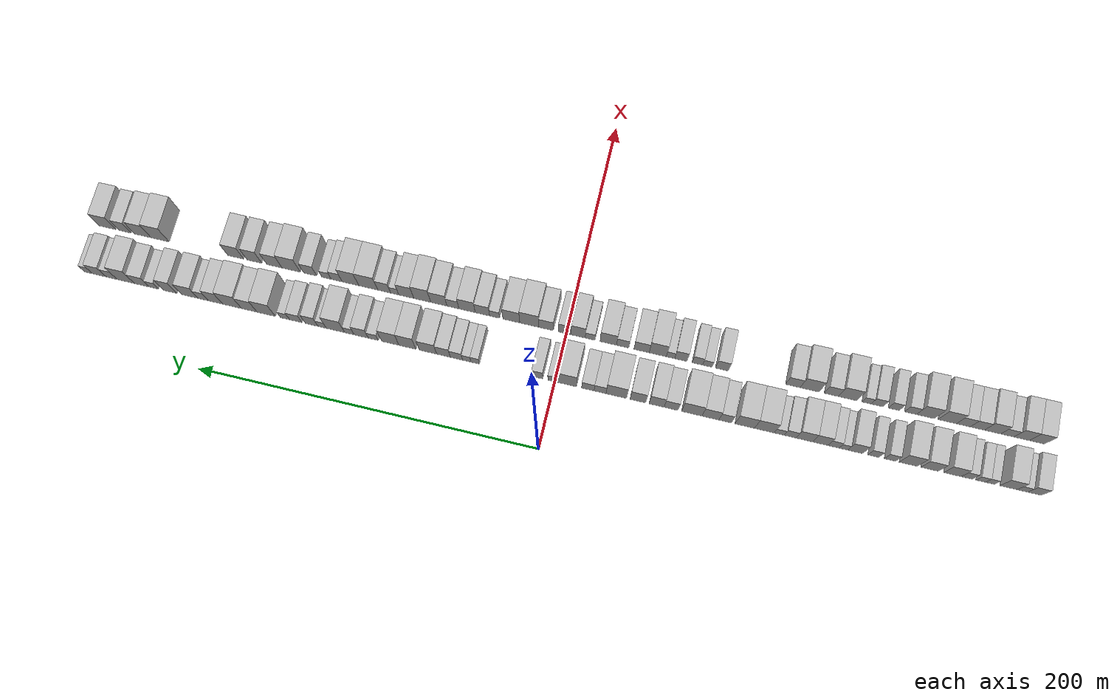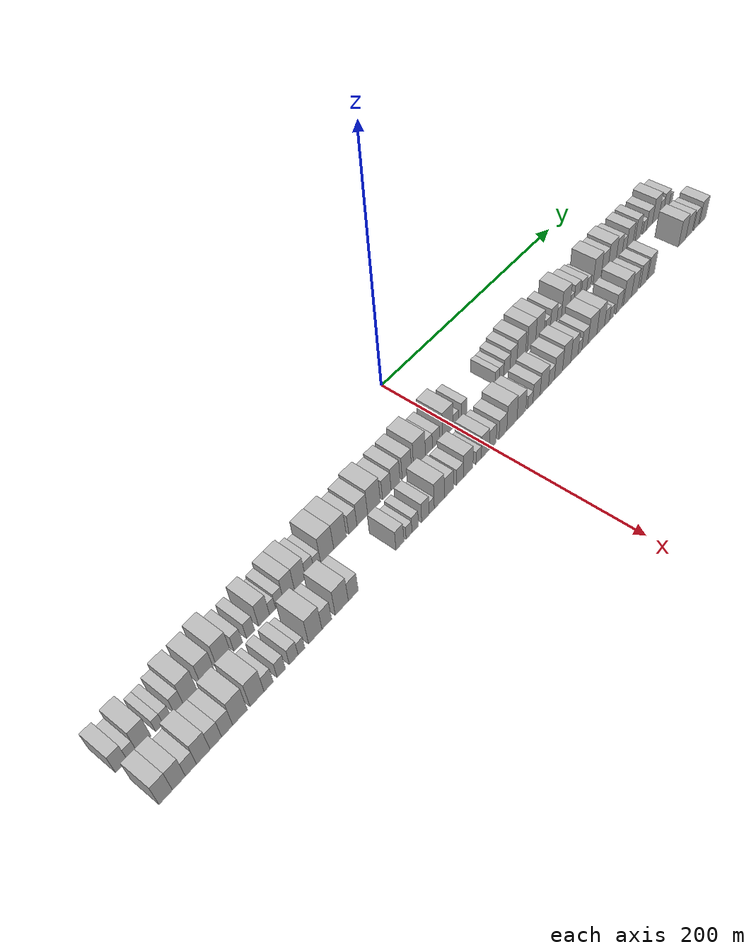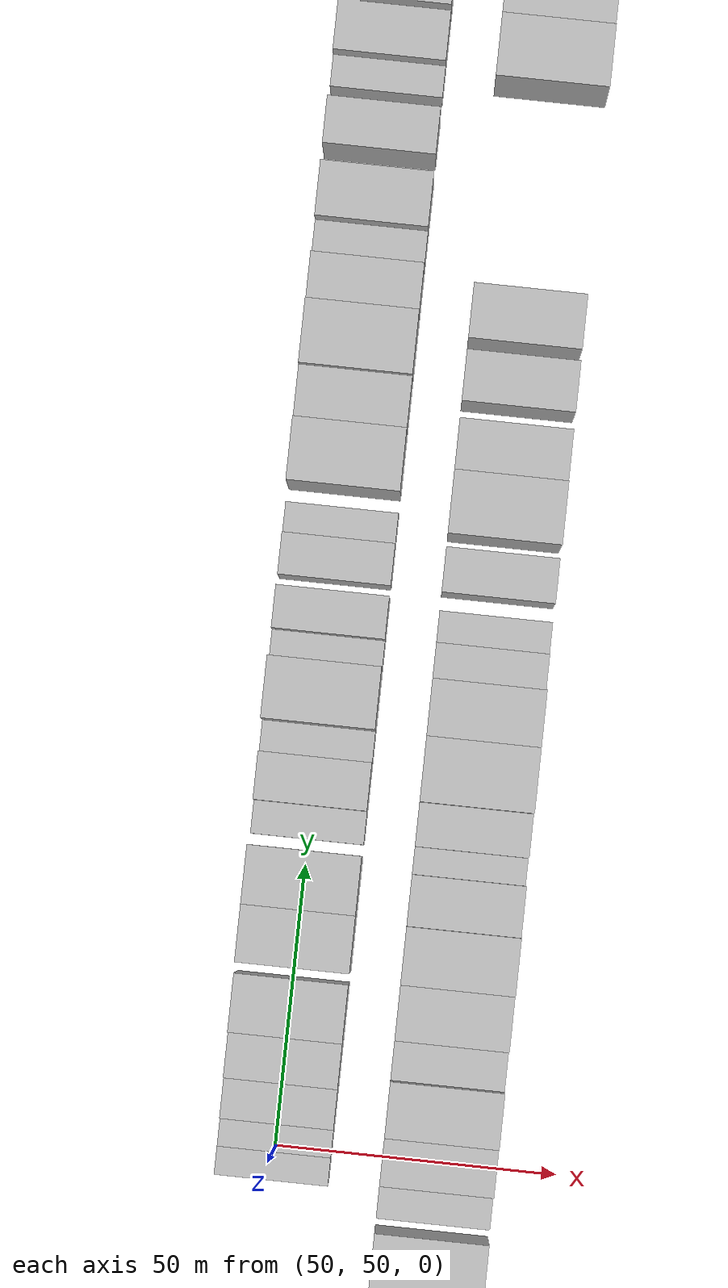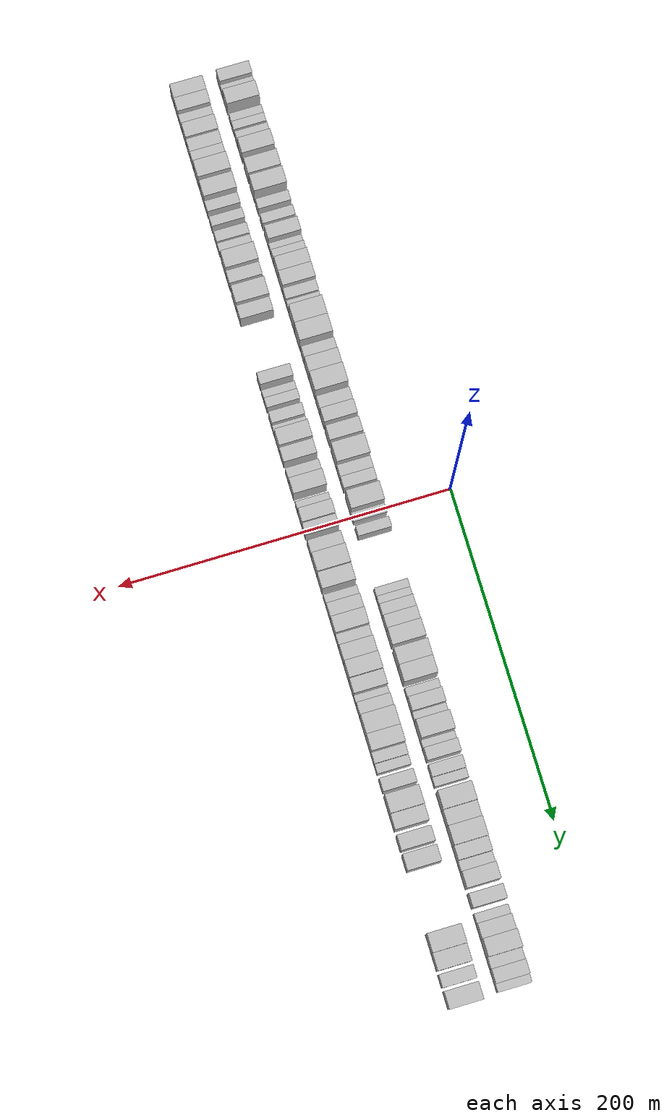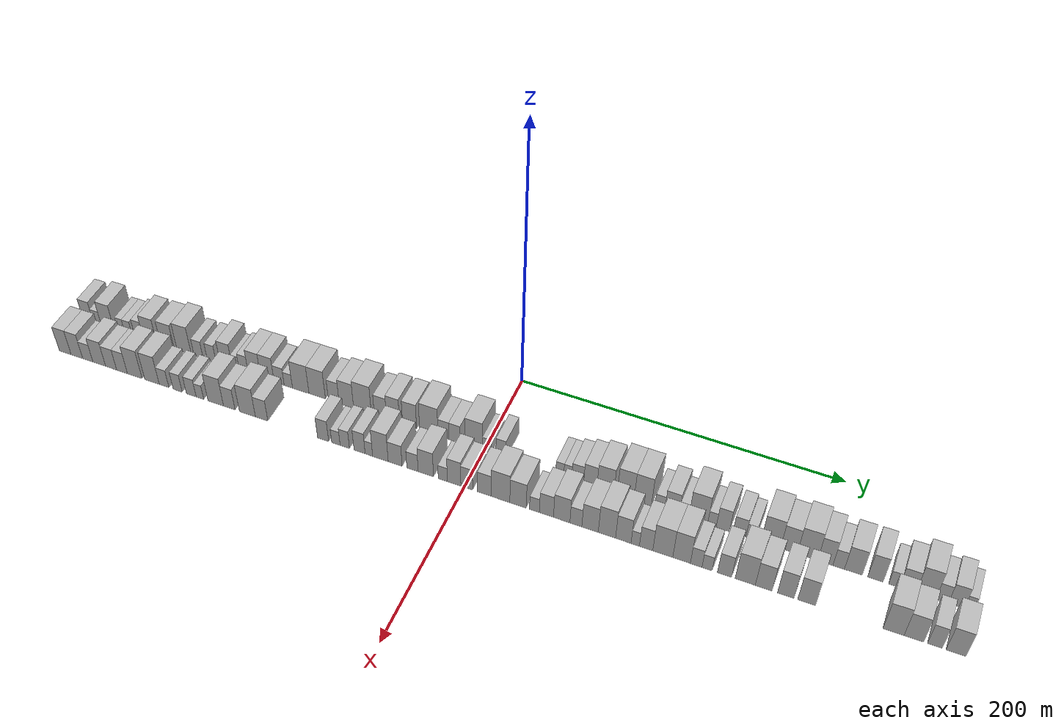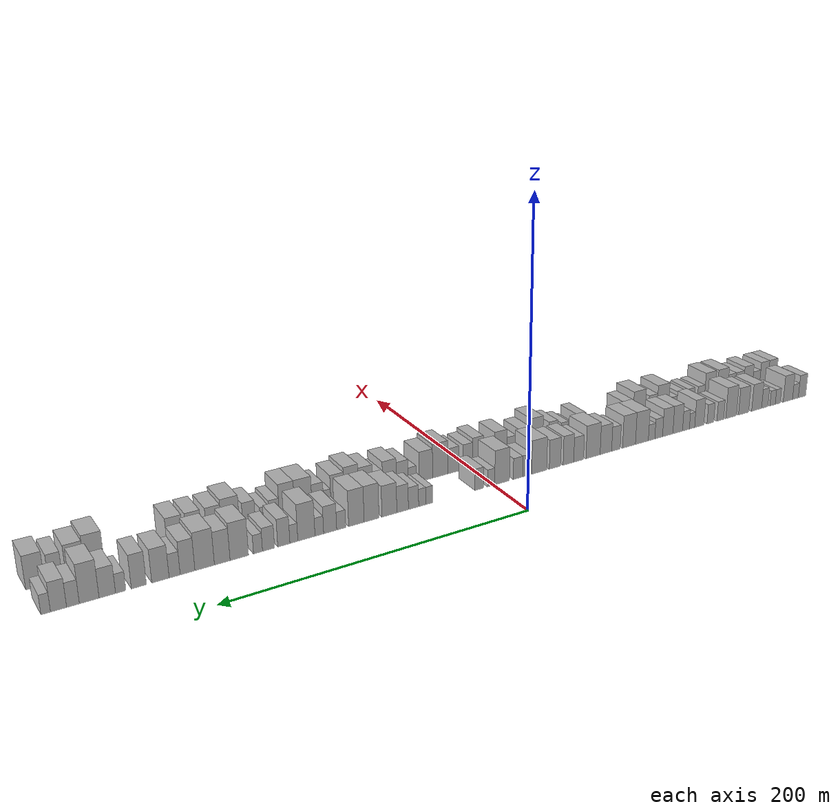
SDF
<sdf version="1.6">
 <world name="default">
  <scene>
   <sky><clouds><speed>12</speed></clouds></sky>
   <ambient>0.4 0.4 0.4 1</ambient>
   <background>0.7 0.7 0.7 1</background>
   <shadows>1</shadows>
  </scene>
  <gravity>0 0 -9.8066</gravity>
  <magnetic_field>6e-06 2.3e-05 -4.2e-05</magnetic_field>
  <physics default="0" name="default_physics" type="ode">
   <ode>
    <solver>
     <type>quick</type>
     <iters>10</iters>
     <sor>1.0</sor>
     <use_dynamic_moi_rescaling>0</use_dynamic_moi_rescaling>
    </solver>
    <constraints>
     <cfm>0</cfm>
     <erp>0.2</erp>
     <contact_max_correcting_vel>100</contact_max_correcting_vel>
     <contact_surface_layer>0.001</contact_surface_layer>
    </constraints>
   </ode>
   <max_step_size>0.004</max_step_size>
   <real_time_factor>1</real_time_factor>
   <real_time_update_rate>250</real_time_update_rate>
  </physics>
  <light name="sun" type="directional">
   <pose>0 0 10 0 0 0</pose>
   <diffuse>0.8 0.8 0.8 1</diffuse>
   <specular>0.2 0.2 0.2 1</specular>
   <attenuation>
    <range>1000</range>
    <constant>0.9</constant>
    <linear>0.01</linear>
    <quadratic>0.001</quadratic>
   </attenuation>
   <direction>-0.5 0.1 -0.9</direction>
  </light>
  <model name="building_1">
   <static>1</static>
   <pose>50.0000 -274.1434 0 0.000000 0.000000 0.000000</pose>
   <link name="link">
    <pose>0 0 9.00 0 0 0</pose>
    <collision name="collision"><geometry><box><size>20.0000 7.7133 18.0000</size></box></geometry></collision>
    <visual name="visual">
     <cast_shadows>0</cast_shadows>
     <geometry><box><size>20.0000 7.7133 18.0000</size></box></geometry>
     <material>
      <script>
       <uri>model://HANNAS_wall/materials/scripts</uri>
       <uri>model://HANNAS_wall/materials/textures</uri>
       <name>vrc/HANNAS_wall</name>
      </script>
     </material>
    </visual>
   </link>
  </model>
  <model name="building_2">
   <static>1</static>
   <pose>50.0000 -267.2990 0 0.000000 0.000000 0.000000</pose>
   <link name="link">
    <pose>0 0 6.00 0 0 0</pose>
    <collision name="collision"><geometry><box><size>20.0000 5.9753 12.0000</size></box></geometry></collision>
    <visual name="visual">
     <cast_shadows>0</cast_shadows>
     <geometry><box><size>20.0000 5.9753 12.0000</size></box></geometry>
     <material>
      <script>
       <uri>model://HANNAS_wall/materials/scripts</uri>
       <uri>model://HANNAS_wall/materials/textures</uri>
       <name>vrc/HANNAS_wall</name>
      </script>
     </material>
    </visual>
   </link>
  </model>
  <model name="building_3">
   <static>1</static>
   <pose>50.0000 -259.5377 0 0.000000 0.000000 0.000000</pose>
   <link name="link">
    <pose>0 0 10.50 0 0 0</pose>
    <collision name="collision"><geometry><box><size>20.0000 9.5473 21.0000</size></box></geometry></collision>
    <visual name="visual">
     <cast_shadows>0</cast_shadows>
     <geometry><box><size>20.0000 9.5473 21.0000</size></box></geometry>
     <material>
      <script>
       <uri>model://HANNAS_wall/materials/scripts</uri>
       <uri>model://HANNAS_wall/materials/textures</uri>
       <name>vrc/HANNAS_wall</name>
      </script>
     </material>
    </visual>
   </link>
  </model>
  <model name="building_4">
   <static>1</static>
   <pose>50.0000 -249.2695 0 0.000000 0.000000 0.000000</pose>
   <link name="link">
    <pose>0 0 6.00 0 0 0</pose>
    <collision name="collision"><geometry><box><size>20.0000 4.9893 12.0000</size></box></geometry></collision>
    <visual name="visual">
     <cast_shadows>0</cast_shadows>
     <geometry><box><size>20.0000 4.9893 12.0000</size></box></geometry>
     <material>
      <script>
       <uri>model://HANNAS_wall/materials/scripts</uri>
       <uri>model://HANNAS_wall/materials/textures</uri>
       <name>vrc/HANNAS_wall</name>
      </script>
     </material>
    </visual>
   </link>
  </model>
  <model name="building_5">
   <static>1</static>
   <pose>50.0000 -244.0601 0 0.000000 0.000000 0.000000</pose>
   <link name="link">
    <pose>0 0 6.00 0 0 0</pose>
    <collision name="collision"><geometry><box><size>20.0000 5.4295 12.0000</size></box></geometry></collision>
    <visual name="visual">
     <cast_shadows>0</cast_shadows>
     <geometry><box><size>20.0000 5.4295 12.0000</size></box></geometry>
     <material>
      <script>
       <uri>model://HANNAS_wall/materials/scripts</uri>
       <uri>model://HANNAS_wall/materials/textures</uri>
       <name>vrc/HANNAS_wall</name>
      </script>
     </material>
    </visual>
   </link>
  </model>
  <model name="building_6">
   <static>1</static>
   <pose>50.0000 -236.2115 0 0.000000 0.000000 0.000000</pose>
   <link name="link">
    <pose>0 0 7.50 0 0 0</pose>
    <collision name="collision"><geometry><box><size>20.0000 6.2675 15.0000</size></box></geometry></collision>
    <visual name="visual">
     <cast_shadows>0</cast_shadows>
     <geometry><box><size>20.0000 6.2675 15.0000</size></box></geometry>
     <material>
      <script>
       <uri>model://HANNAS_wall/materials/scripts</uri>
       <uri>model://HANNAS_wall/materials/textures</uri>
       <name>vrc/HANNAS_wall</name>
      </script>
     </material>
    </visual>
   </link>
  </model>
  <model name="building_7">
   <static>1</static>
   <pose>50.0000 -228.1773 0 0.000000 0.000000 0.000000</pose>
   <link name="link">
    <pose>0 0 10.50 0 0 0</pose>
    <collision name="collision"><geometry><box><size>20.0000 9.8010 21.0000</size></box></geometry></collision>
    <visual name="visual">
     <cast_shadows>0</cast_shadows>
     <geometry><box><size>20.0000 9.8010 21.0000</size></box></geometry>
     <material>
      <script>
       <uri>model://HANNAS_wall/materials/scripts</uri>
       <uri>model://HANNAS_wall/materials/textures</uri>
       <name>vrc/HANNAS_wall</name>
      </script>
     </material>
    </visual>
   </link>
  </model>
  <model name="building_8">
   <static>1</static>
   <pose>50.0000 -215.3446 0 0.000000 0.000000 0.000000</pose>
   <link name="link">
    <pose>0 0 10.50 0 0 0</pose>
    <collision name="collision"><geometry><box><size>20.0000 9.8645 21.0000</size></box></geometry></collision>
    <visual name="visual">
     <cast_shadows>0</cast_shadows>
     <geometry><box><size>20.0000 9.8645 21.0000</size></box></geometry>
     <material>
      <script>
       <uri>model://HANNAS_wall/materials/scripts</uri>
       <uri>model://HANNAS_wall/materials/textures</uri>
       <name>vrc/HANNAS_wall</name>
      </script>
     </material>
    </visual>
   </link>
  </model>
  <model name="building_9">
   <static>1</static>
   <pose>50.0000 -203.2781 0 0.000000 0.000000 0.000000</pose>
   <link name="link">
    <pose>0 0 12.00 0 0 0</pose>
    <collision name="collision"><geometry><box><size>20.0000 10.2684 24.0000</size></box></geometry></collision>
    <visual name="visual">
     <cast_shadows>0</cast_shadows>
     <geometry><box><size>20.0000 10.2684 24.0000</size></box></geometry>
     <material>
      <script>
       <uri>model://HANNAS_wall/materials/scripts</uri>
       <uri>model://HANNAS_wall/materials/textures</uri>
       <name>vrc/HANNAS_wall</name>
      </script>
     </material>
    </visual>
   </link>
  </model>
  <model name="building_10">
   <static>1</static>
   <pose>50.0000 -192.9101 0 0.000000 0.000000 0.000000</pose>
   <link name="link">
    <pose>0 0 7.50 0 0 0</pose>
    <collision name="collision"><geometry><box><size>20.0000 6.4676 15.0000</size></box></geometry></collision>
    <visual name="visual">
     <cast_shadows>0</cast_shadows>
     <geometry><box><size>20.0000 6.4676 15.0000</size></box></geometry>
     <material>
      <script>
       <uri>model://HANNAS_wall/materials/scripts</uri>
       <uri>model://HANNAS_wall/materials/textures</uri>
       <name>vrc/HANNAS_wall</name>
      </script>
     </material>
    </visual>
   </link>
  </model>
  <model name="building_11">
   <static>1</static>
   <pose>50.0000 -183.5272 0 0.000000 0.000000 0.000000</pose>
   <link name="link">
    <pose>0 0 7.50 0 0 0</pose>
    <collision name="collision"><geometry><box><size>20.0000 6.2981 15.0000</size></box></geometry></collision>
    <visual name="visual">
     <cast_shadows>0</cast_shadows>
     <geometry><box><size>20.0000 6.2981 15.0000</size></box></geometry>
     <material>
      <script>
       <uri>model://HANNAS_wall/materials/scripts</uri>
       <uri>model://HANNAS_wall/materials/textures</uri>
       <name>vrc/HANNAS_wall</name>
      </script>
     </material>
    </visual>
   </link>
  </model>
  <model name="building_12">
   <static>1</static>
   <pose>50.0000 -173.1050 0 0.000000 0.000000 0.000000</pose>
   <link name="link">
    <pose>0 0 10.50 0 0 0</pose>
    <collision name="collision"><geometry><box><size>20.0000 8.5462 21.0000</size></box></geometry></collision>
    <visual name="visual">
     <cast_shadows>0</cast_shadows>
     <geometry><box><size>20.0000 8.5462 21.0000</size></box></geometry>
     <material>
      <script>
       <uri>model://HANNAS_wall/materials/scripts</uri>
       <uri>model://HANNAS_wall/materials/textures</uri>
       <name>vrc/HANNAS_wall</name>
      </script>
     </material>
    </visual>
   </link>
  </model>
  <model name="building_13">
   <static>1</static>
   <pose>50.0000 -166.3974 0 0.000000 0.000000 0.000000</pose>
   <link name="link">
    <pose>0 0 6.00 0 0 0</pose>
    <collision name="collision"><geometry><box><size>20.0000 4.8691 12.0000</size></box></geometry></collision>
    <visual name="visual">
     <cast_shadows>0</cast_shadows>
     <geometry><box><size>20.0000 4.8691 12.0000</size></box></geometry>
     <material>
      <script>
       <uri>model://HANNAS_wall/materials/scripts</uri>
       <uri>model://HANNAS_wall/materials/textures</uri>
       <name>vrc/HANNAS_wall</name>
      </script>
     </material>
    </visual>
   </link>
  </model>
  <model name="building_14">
   <static>1</static>
   <pose>50.0000 -160.8092 0 0.000000 0.000000 0.000000</pose>
   <link name="link">
    <pose>0 0 7.50 0 0 0</pose>
    <collision name="collision"><geometry><box><size>20.0000 6.3073 15.0000</size></box></geometry></collision>
    <visual name="visual">
     <cast_shadows>0</cast_shadows>
     <geometry><box><size>20.0000 6.3073 15.0000</size></box></geometry>
     <material>
      <script>
       <uri>model://HANNAS_wall/materials/scripts</uri>
       <uri>model://HANNAS_wall/materials/textures</uri>
       <name>vrc/HANNAS_wall</name>
      </script>
     </material>
    </visual>
   </link>
  </model>
  <model name="building_15">
   <static>1</static>
   <pose>50.0000 -153.2628 0 0.000000 0.000000 0.000000</pose>
   <link name="link">
    <pose>0 0 10.50 0 0 0</pose>
    <collision name="collision"><geometry><box><size>20.0000 8.7855 21.0000</size></box></geometry></collision>
    <visual name="visual">
     <cast_shadows>0</cast_shadows>
     <geometry><box><size>20.0000 8.7855 21.0000</size></box></geometry>
     <material>
      <script>
       <uri>model://HANNAS_wall/materials/scripts</uri>
       <uri>model://HANNAS_wall/materials/textures</uri>
       <name>vrc/HANNAS_wall</name>
      </script>
     </material>
    </visual>
   </link>
  </model>
  <model name="building_16">
   <static>1</static>
   <pose>50.0000 -144.2227 0 0.000000 0.000000 0.000000</pose>
   <link name="link">
    <pose>0 0 10.50 0 0 0</pose>
    <collision name="collision"><geometry><box><size>20.0000 9.2948 21.0000</size></box></geometry></collision>
    <visual name="visual">
     <cast_shadows>0</cast_shadows>
     <geometry><box><size>20.0000 9.2948 21.0000</size></box></geometry>
     <material>
      <script>
       <uri>model://HANNAS_wall/materials/scripts</uri>
       <uri>model://HANNAS_wall/materials/textures</uri>
       <name>vrc/HANNAS_wall</name>
      </script>
     </material>
    </visual>
   </link>
  </model>
  <model name="building_17">
   <static>1</static>
   <pose>50.0000 -136.1297 0 0.000000 0.000000 0.000000</pose>
   <link name="link">
    <pose>0 0 7.50 0 0 0</pose>
    <collision name="collision"><geometry><box><size>20.0000 6.8911 15.0000</size></box></geometry></collision>
    <visual name="visual">
     <cast_shadows>0</cast_shadows>
     <geometry><box><size>20.0000 6.8911 15.0000</size></box></geometry>
     <material>
      <script>
       <uri>model://HANNAS_wall/materials/scripts</uri>
       <uri>model://HANNAS_wall/materials/textures</uri>
       <name>vrc/HANNAS_wall</name>
      </script>
     </material>
    </visual>
   </link>
  </model>
  <model name="building_18">
   <static>1</static>
   <pose>50.0000 -129.8239 0 0.000000 0.000000 0.000000</pose>
   <link name="link">
    <pose>0 0 6.00 0 0 0</pose>
    <collision name="collision"><geometry><box><size>20.0000 5.7206 12.0000</size></box></geometry></collision>
    <visual name="visual">
     <cast_shadows>0</cast_shadows>
     <geometry><box><size>20.0000 5.7206 12.0000</size></box></geometry>
     <material>
      <script>
       <uri>model://HANNAS_wall/materials/scripts</uri>
       <uri>model://HANNAS_wall/materials/textures</uri>
       <name>vrc/HANNAS_wall</name>
      </script>
     </material>
    </visual>
   </link>
  </model>
  <model name="building_19">
   <static>1</static>
   <pose>50.0000 -121.2929 0 0.000000 0.000000 0.000000</pose>
   <link name="link">
    <pose>0 0 12.00 0 0 0</pose>
    <collision name="collision"><geometry><box><size>20.0000 11.3414 24.0000</size></box></geometry></collision>
    <visual name="visual">
     <cast_shadows>0</cast_shadows>
     <geometry><box><size>20.0000 11.3414 24.0000</size></box></geometry>
     <material>
      <script>
       <uri>model://HANNAS_wall/materials/scripts</uri>
       <uri>model://HANNAS_wall/materials/textures</uri>
       <name>vrc/HANNAS_wall</name>
      </script>
     </material>
    </visual>
   </link>
  </model>
  <model name="building_20">
   <static>1</static>
   <pose>50.0000 -110.0250 0 0.000000 0.000000 0.000000</pose>
   <link name="link">
    <pose>0 0 12.00 0 0 0</pose>
    <collision name="collision"><geometry><box><size>20.0000 11.1943 24.0000</size></box></geometry></collision>
    <visual name="visual">
     <cast_shadows>0</cast_shadows>
     <geometry><box><size>20.0000 11.1943 24.0000</size></box></geometry>
     <material>
      <script>
       <uri>model://HANNAS_wall/materials/scripts</uri>
       <uri>model://HANNAS_wall/materials/textures</uri>
       <name>vrc/HANNAS_wall</name>
      </script>
     </material>
    </visual>
   </link>
  </model>
  <model name="building_21">
   <static>1</static>
   <pose>50.0000 -98.7826 0 0.000000 0.000000 0.000000</pose>
   <link name="link">
    <pose>0 0 9.00 0 0 0</pose>
    <collision name="collision"><geometry><box><size>20.0000 7.2906 18.0000</size></box></geometry></collision>
    <visual name="visual">
     <cast_shadows>0</cast_shadows>
     <geometry><box><size>20.0000 7.2906 18.0000</size></box></geometry>
     <material>
      <script>
       <uri>model://HANNAS_wall/materials/scripts</uri>
       <uri>model://HANNAS_wall/materials/textures</uri>
       <name>vrc/HANNAS_wall</name>
      </script>
     </material>
    </visual>
   </link>
  </model>
  <model name="building_22">
   <static>1</static>
   <pose>50.0000 -90.2696 0 0.000000 0.000000 0.000000</pose>
   <link name="link">
    <pose>0 0 10.50 0 0 0</pose>
    <collision name="collision"><geometry><box><size>20.0000 9.7353 21.0000</size></box></geometry></collision>
    <visual name="visual">
     <cast_shadows>0</cast_shadows>
     <geometry><box><size>20.0000 9.7353 21.0000</size></box></geometry>
     <material>
      <script>
       <uri>model://HANNAS_wall/materials/scripts</uri>
       <uri>model://HANNAS_wall/materials/textures</uri>
       <name>vrc/HANNAS_wall</name>
      </script>
     </material>
    </visual>
   </link>
  </model>
  <model name="building_23">
   <static>1</static>
   <pose>50.0000 -79.4878 0 0.000000 0.000000 0.000000</pose>
   <link name="link">
    <pose>0 0 12.00 0 0 0</pose>
    <collision name="collision"><geometry><box><size>20.0000 11.8283 24.0000</size></box></geometry></collision>
    <visual name="visual">
     <cast_shadows>0</cast_shadows>
     <geometry><box><size>20.0000 11.8283 24.0000</size></box></geometry>
     <material>
      <script>
       <uri>model://HANNAS_wall/materials/scripts</uri>
       <uri>model://HANNAS_wall/materials/textures</uri>
       <name>vrc/HANNAS_wall</name>
      </script>
     </material>
    </visual>
   </link>
  </model>
  <model name="building_24">
   <static>1</static>
   <pose>50.0000 -67.5209 0 0.000000 0.000000 0.000000</pose>
   <link name="link">
    <pose>0 0 9.00 0 0 0</pose>
    <collision name="collision"><geometry><box><size>20.0000 8.1056 18.0000</size></box></geometry></collision>
    <visual name="visual">
     <cast_shadows>0</cast_shadows>
     <geometry><box><size>20.0000 8.1056 18.0000</size></box></geometry>
     <material>
      <script>
       <uri>model://HANNAS_wall/materials/scripts</uri>
       <uri>model://HANNAS_wall/materials/textures</uri>
       <name>vrc/HANNAS_wall</name>
      </script>
     </material>
    </visual>
   </link>
  </model>
  <model name="building_25">
   <static>1</static>
   <pose>50.0000 -59.1467 0 0.000000 0.000000 0.000000</pose>
   <link name="link">
    <pose>0 0 10.50 0 0 0</pose>
    <collision name="collision"><geometry><box><size>20.0000 8.6426 21.0000</size></box></geometry></collision>
    <visual name="visual">
     <cast_shadows>0</cast_shadows>
     <geometry><box><size>20.0000 8.6426 21.0000</size></box></geometry>
     <material>
      <script>
       <uri>model://HANNAS_wall/materials/scripts</uri>
       <uri>model://HANNAS_wall/materials/textures</uri>
       <name>vrc/HANNAS_wall</name>
      </script>
     </material>
    </visual>
   </link>
  </model>
  <model name="building_26">
   <static>1</static>
   <pose>50.0000 -48.2642 0 0.000000 0.000000 0.000000</pose>
   <link name="link">
    <pose>0 0 10.50 0 0 0</pose>
    <collision name="collision"><geometry><box><size>20.0000 9.1225 21.0000</size></box></geometry></collision>
    <visual name="visual">
     <cast_shadows>0</cast_shadows>
     <geometry><box><size>20.0000 9.1225 21.0000</size></box></geometry>
     <material>
      <script>
       <uri>model://HANNAS_wall/materials/scripts</uri>
       <uri>model://HANNAS_wall/materials/textures</uri>
       <name>vrc/HANNAS_wall</name>
      </script>
     </material>
    </visual>
   </link>
  </model>
  <model name="building_27">
   <static>1</static>
   <pose>50.0000 -35.7431 0 0.000000 0.000000 0.000000</pose>
   <link name="link">
    <pose>0 0 12.00 0 0 0</pose>
    <collision name="collision"><geometry><box><size>20.0000 11.9196 24.0000</size></box></geometry></collision>
    <visual name="visual">
     <cast_shadows>0</cast_shadows>
     <geometry><box><size>20.0000 11.9196 24.0000</size></box></geometry>
     <material>
      <script>
       <uri>model://HANNAS_wall/materials/scripts</uri>
       <uri>model://HANNAS_wall/materials/textures</uri>
       <name>vrc/HANNAS_wall</name>
      </script>
     </material>
    </visual>
   </link>
  </model>
  <model name="building_28">
   <static>1</static>
   <pose>50.0000 -26.2708 0 0.000000 0.000000 0.000000</pose>
   <link name="link">
    <pose>0 0 7.50 0 0 0</pose>
    <collision name="collision"><geometry><box><size>20.0000 7.0249 15.0000</size></box></geometry></collision>
    <visual name="visual">
     <cast_shadows>0</cast_shadows>
     <geometry><box><size>20.0000 7.0249 15.0000</size></box></geometry>
     <material>
      <script>
       <uri>model://HANNAS_wall/materials/scripts</uri>
       <uri>model://HANNAS_wall/materials/textures</uri>
       <name>vrc/HANNAS_wall</name>
      </script>
     </material>
    </visual>
   </link>
  </model>
  <model name="building_29">
   <static>1</static>
   <pose>50.0000 -19.1075 0 0.000000 0.000000 0.000000</pose>
   <link name="link">
    <pose>0 0 7.50 0 0 0</pose>
    <collision name="collision"><geometry><box><size>20.0000 7.3019 15.0000</size></box></geometry></collision>
    <visual name="visual">
     <cast_shadows>0</cast_shadows>
     <geometry><box><size>20.0000 7.3019 15.0000</size></box></geometry>
     <material>
      <script>
       <uri>model://HANNAS_wall/materials/scripts</uri>
       <uri>model://HANNAS_wall/materials/textures</uri>
       <name>vrc/HANNAS_wall</name>
      </script>
     </material>
    </visual>
   </link>
  </model>
  <model name="building_30">
   <static>1</static>
   <pose>50.0000 -6.8687 0 0.000000 0.000000 0.000000</pose>
   <link name="link">
    <pose>0 0 12.00 0 0 0</pose>
    <collision name="collision"><geometry><box><size>20.0000 11.1757 24.0000</size></box></geometry></collision>
    <visual name="visual">
     <cast_shadows>0</cast_shadows>
     <geometry><box><size>20.0000 11.1757 24.0000</size></box></geometry>
     <material>
      <script>
       <uri>model://HANNAS_wall/materials/scripts</uri>
       <uri>model://HANNAS_wall/materials/textures</uri>
       <name>vrc/HANNAS_wall</name>
      </script>
     </material>
    </visual>
   </link>
  </model>
  <model name="building_31">
   <static>1</static>
   <pose>50.0000 1.4991 0 0.000000 0.000000 0.000000</pose>
   <link name="link">
    <pose>0 0 6.00 0 0 0</pose>
    <collision name="collision"><geometry><box><size>20.0000 5.5599 12.0000</size></box></geometry></collision>
    <visual name="visual">
     <cast_shadows>0</cast_shadows>
     <geometry><box><size>20.0000 5.5599 12.0000</size></box></geometry>
     <material>
      <script>
       <uri>model://HANNAS_wall/materials/scripts</uri>
       <uri>model://HANNAS_wall/materials/textures</uri>
       <name>vrc/HANNAS_wall</name>
      </script>
     </material>
    </visual>
   </link>
  </model>
  <model name="building_32">
   <static>1</static>
   <pose>50.0000 10.4572 0 0.000000 0.000000 0.000000</pose>
   <link name="link">
    <pose>0 0 7.50 0 0 0</pose>
    <collision name="collision"><geometry><box><size>20.0000 6.3563 15.0000</size></box></geometry></collision>
    <visual name="visual">
     <cast_shadows>0</cast_shadows>
     <geometry><box><size>20.0000 6.3563 15.0000</size></box></geometry>
     <material>
      <script>
       <uri>model://HANNAS_wall/materials/scripts</uri>
       <uri>model://HANNAS_wall/materials/textures</uri>
       <name>vrc/HANNAS_wall</name>
      </script>
     </material>
    </visual>
   </link>
  </model>
  <model name="building_33">
   <static>1</static>
   <pose>50.0000 47.0578 0 0.000000 0.000000 0.000000</pose>
   <link name="link">
    <pose>0 0 6.00 0 0 0</pose>
    <collision name="collision"><geometry><box><size>20.0000 4.9483 12.0000</size></box></geometry></collision>
    <visual name="visual">
     <cast_shadows>0</cast_shadows>
     <geometry><box><size>20.0000 4.9483 12.0000</size></box></geometry>
     <material>
      <script>
       <uri>model://HANNAS_wall/materials/scripts</uri>
       <uri>model://HANNAS_wall/materials/textures</uri>
       <name>vrc/HANNAS_wall</name>
      </script>
     </material>
    </visual>
   </link>
  </model>
  <model name="building_34">
   <static>1</static>
   <pose>50.0000 52.0411 0 0.000000 0.000000 0.000000</pose>
   <link name="link">
    <pose>0 0 6.00 0 0 0</pose>
    <collision name="collision"><geometry><box><size>20.0000 5.0184 12.0000</size></box></geometry></collision>
    <visual name="visual">
     <cast_shadows>0</cast_shadows>
     <geometry><box><size>20.0000 5.0184 12.0000</size></box></geometry>
     <material>
      <script>
       <uri>model://HANNAS_wall/materials/scripts</uri>
       <uri>model://HANNAS_wall/materials/textures</uri>
       <name>vrc/HANNAS_wall</name>
      </script>
     </material>
    </visual>
   </link>
  </model>
  <model name="building_35">
   <static>1</static>
   <pose>50.0000 58.1626 0 0.000000 0.000000 0.000000</pose>
   <link name="link">
    <pose>0 0 7.50 0 0 0</pose>
    <collision name="collision"><geometry><box><size>20.0000 7.2245 15.0000</size></box></geometry></collision>
    <visual name="visual">
     <cast_shadows>0</cast_shadows>
     <geometry><box><size>20.0000 7.2245 15.0000</size></box></geometry>
     <material>
      <script>
       <uri>model://HANNAS_wall/materials/scripts</uri>
       <uri>model://HANNAS_wall/materials/textures</uri>
       <name>vrc/HANNAS_wall</name>
      </script>
     </material>
    </visual>
   </link>
  </model>
  <model name="building_36">
   <static>1</static>
   <pose>50.0000 65.8021 0 0.000000 0.000000 0.000000</pose>
   <link name="link">
    <pose>0 0 9.00 0 0 0</pose>
    <collision name="collision"><geometry><box><size>20.0000 8.0544 18.0000</size></box></geometry></collision>
    <visual name="visual">
     <cast_shadows>0</cast_shadows>
     <geometry><box><size>20.0000 8.0544 18.0000</size></box></geometry>
     <material>
      <script>
       <uri>model://HANNAS_wall/materials/scripts</uri>
       <uri>model://HANNAS_wall/materials/textures</uri>
       <name>vrc/HANNAS_wall</name>
      </script>
     </material>
    </visual>
   </link>
  </model>
  <model name="building_37">
   <static>1</static>
   <pose>50.0000 74.9746 0 0.000000 0.000000 0.000000</pose>
   <link name="link">
    <pose>0 0 10.50 0 0 0</pose>
    <collision name="collision"><geometry><box><size>20.0000 10.2906 21.0000</size></box></geometry></collision>
    <visual name="visual">
     <cast_shadows>0</cast_shadows>
     <geometry><box><size>20.0000 10.2906 21.0000</size></box></geometry>
     <material>
      <script>
       <uri>model://HANNAS_wall/materials/scripts</uri>
       <uri>model://HANNAS_wall/materials/textures</uri>
       <name>vrc/HANNAS_wall</name>
      </script>
     </material>
    </visual>
   </link>
  </model>
  <model name="building_38">
   <static>1</static>
   <pose>50.0000 87.1517 0 0.000000 0.000000 0.000000</pose>
   <link name="link">
    <pose>0 0 12.00 0 0 0</pose>
    <collision name="collision"><geometry><box><size>20.0000 10.0634 24.0000</size></box></geometry></collision>
    <visual name="visual">
     <cast_shadows>0</cast_shadows>
     <geometry><box><size>20.0000 10.0634 24.0000</size></box></geometry>
     <material>
      <script>
       <uri>model://HANNAS_wall/materials/scripts</uri>
       <uri>model://HANNAS_wall/materials/textures</uri>
       <name>vrc/HANNAS_wall</name>
      </script>
     </material>
    </visual>
   </link>
  </model>
  <model name="building_39">
   <static>1</static>
   <pose>50.0000 97.3643 0 0.000000 0.000000 0.000000</pose>
   <link name="link">
    <pose>0 0 12.00 0 0 0</pose>
    <collision name="collision"><geometry><box><size>20.0000 10.3618 24.0000</size></box></geometry></collision>
    <visual name="visual">
     <cast_shadows>0</cast_shadows>
     <geometry><box><size>20.0000 10.3618 24.0000</size></box></geometry>
     <material>
      <script>
       <uri>model://HANNAS_wall/materials/scripts</uri>
       <uri>model://HANNAS_wall/materials/textures</uri>
       <name>vrc/HANNAS_wall</name>
      </script>
     </material>
    </visual>
   </link>
  </model>
  <model name="building_40">
   <static>1</static>
   <pose>50.0000 107.4989 0 0.000000 0.000000 0.000000</pose>
   <link name="link">
    <pose>0 0 6.00 0 0 0</pose>
    <collision name="collision"><geometry><box><size>20.0000 5.9075 12.0000</size></box></geometry></collision>
    <visual name="visual">
     <cast_shadows>0</cast_shadows>
     <geometry><box><size>20.0000 5.9075 12.0000</size></box></geometry>
     <material>
      <script>
       <uri>model://HANNAS_wall/materials/scripts</uri>
       <uri>model://HANNAS_wall/materials/textures</uri>
       <name>vrc/HANNAS_wall</name>
      </script>
     </material>
    </visual>
   </link>
  </model>
  <model name="building_41">
   <static>1</static>
   <pose>50.0000 114.7138 0 0.000000 0.000000 0.000000</pose>
   <link name="link">
    <pose>0 0 9.00 0 0 0</pose>
    <collision name="collision"><geometry><box><size>20.0000 8.5223 18.0000</size></box></geometry></collision>
    <visual name="visual">
     <cast_shadows>0</cast_shadows>
     <geometry><box><size>20.0000 8.5223 18.0000</size></box></geometry>
     <material>
      <script>
       <uri>model://HANNAS_wall/materials/scripts</uri>
       <uri>model://HANNAS_wall/materials/textures</uri>
       <name>vrc/HANNAS_wall</name>
      </script>
     </material>
    </visual>
   </link>
  </model>
  <model name="building_42">
   <static>1</static>
   <pose>50.0000 121.7857 0 0.000000 0.000000 0.000000</pose>
   <link name="link">
    <pose>0 0 6.00 0 0 0</pose>
    <collision name="collision"><geometry><box><size>20.0000 5.6216 12.0000</size></box></geometry></collision>
    <visual name="visual">
     <cast_shadows>0</cast_shadows>
     <geometry><box><size>20.0000 5.6216 12.0000</size></box></geometry>
     <material>
      <script>
       <uri>model://HANNAS_wall/materials/scripts</uri>
       <uri>model://HANNAS_wall/materials/textures</uri>
       <name>vrc/HANNAS_wall</name>
      </script>
     </material>
    </visual>
   </link>
  </model>
  <model name="building_43">
   <static>1</static>
   <pose>50.0000 130.0969 0 0.000000 0.000000 0.000000</pose>
   <link name="link">
    <pose>0 0 12.00 0 0 0</pose>
    <collision name="collision"><geometry><box><size>20.0000 11.0009 24.0000</size></box></geometry></collision>
    <visual name="visual">
     <cast_shadows>0</cast_shadows>
     <geometry><box><size>20.0000 11.0009 24.0000</size></box></geometry>
     <material>
      <script>
       <uri>model://HANNAS_wall/materials/scripts</uri>
       <uri>model://HANNAS_wall/materials/textures</uri>
       <name>vrc/HANNAS_wall</name>
      </script>
     </material>
    </visual>
   </link>
  </model>
  <model name="building_44">
   <static>1</static>
   <pose>50.0000 138.1071 0 0.000000 0.000000 0.000000</pose>
   <link name="link">
    <pose>0 0 6.00 0 0 0</pose>
    <collision name="collision"><geometry><box><size>20.0000 5.0195 12.0000</size></box></geometry></collision>
    <visual name="visual">
     <cast_shadows>0</cast_shadows>
     <geometry><box><size>20.0000 5.0195 12.0000</size></box></geometry>
     <material>
      <script>
       <uri>model://HANNAS_wall/materials/scripts</uri>
       <uri>model://HANNAS_wall/materials/textures</uri>
       <name>vrc/HANNAS_wall</name>
      </script>
     </material>
    </visual>
   </link>
  </model>
  <model name="building_45">
   <static>1</static>
   <pose>50.0000 144.4214 0 0.000000 0.000000 0.000000</pose>
   <link name="link">
    <pose>0 0 9.00 0 0 0</pose>
    <collision name="collision"><geometry><box><size>20.0000 7.6092 18.0000</size></box></geometry></collision>
    <visual name="visual">
     <cast_shadows>0</cast_shadows>
     <geometry><box><size>20.0000 7.6092 18.0000</size></box></geometry>
     <material>
      <script>
       <uri>model://HANNAS_wall/materials/scripts</uri>
       <uri>model://HANNAS_wall/materials/textures</uri>
       <name>vrc/HANNAS_wall</name>
      </script>
     </material>
    </visual>
   </link>
  </model>
  <model name="building_46">
   <static>1</static>
   <pose>50.0000 153.9650 0 0.000000 0.000000 0.000000</pose>
   <link name="link">
    <pose>0 0 7.50 0 0 0</pose>
    <collision name="collision"><geometry><box><size>20.0000 7.4780 15.0000</size></box></geometry></collision>
    <visual name="visual">
     <cast_shadows>0</cast_shadows>
     <geometry><box><size>20.0000 7.4780 15.0000</size></box></geometry>
     <material>
      <script>
       <uri>model://HANNAS_wall/materials/scripts</uri>
       <uri>model://HANNAS_wall/materials/textures</uri>
       <name>vrc/HANNAS_wall</name>
      </script>
     </material>
    </visual>
   </link>
  </model>
  <model name="building_47">
   <static>1</static>
   <pose>50.0000 160.4777 0 0.000000 0.000000 0.000000</pose>
   <link name="link">
    <pose>0 0 6.00 0 0 0</pose>
    <collision name="collision"><geometry><box><size>20.0000 5.5474 12.0000</size></box></geometry></collision>
    <visual name="visual">
     <cast_shadows>0</cast_shadows>
     <geometry><box><size>20.0000 5.5474 12.0000</size></box></geometry>
     <material>
      <script>
       <uri>model://HANNAS_wall/materials/scripts</uri>
       <uri>model://HANNAS_wall/materials/textures</uri>
       <name>vrc/HANNAS_wall</name>
      </script>
     </material>
    </visual>
   </link>
  </model>
  <model name="building_48">
   <static>1</static>
   <pose>50.0000 171.8402 0 0.000000 0.000000 0.000000</pose>
   <link name="link">
    <pose>0 0 12.00 0 0 0</pose>
    <collision name="collision"><geometry><box><size>20.0000 11.1776 24.0000</size></box></geometry></collision>
    <visual name="visual">
     <cast_shadows>0</cast_shadows>
     <geometry><box><size>20.0000 11.1776 24.0000</size></box></geometry>
     <material>
      <script>
       <uri>model://HANNAS_wall/materials/scripts</uri>
       <uri>model://HANNAS_wall/materials/textures</uri>
       <name>vrc/HANNAS_wall</name>
      </script>
     </material>
    </visual>
   </link>
  </model>
  <model name="building_49">
   <static>1</static>
   <pose>50.0000 182.1017 0 0.000000 0.000000 0.000000</pose>
   <link name="link">
    <pose>0 0 10.50 0 0 0</pose>
    <collision name="collision"><geometry><box><size>20.0000 9.3454 21.0000</size></box></geometry></collision>
    <visual name="visual">
     <cast_shadows>0</cast_shadows>
     <geometry><box><size>20.0000 9.3454 21.0000</size></box></geometry>
     <material>
      <script>
       <uri>model://HANNAS_wall/materials/scripts</uri>
       <uri>model://HANNAS_wall/materials/textures</uri>
       <name>vrc/HANNAS_wall</name>
      </script>
     </material>
    </visual>
   </link>
  </model>
  <model name="building_50">
   <static>1</static>
   <pose>50.0000 192.4914 0 0.000000 0.000000 0.000000</pose>
   <link name="link">
    <pose>0 0 12.00 0 0 0</pose>
    <collision name="collision"><geometry><box><size>20.0000 11.4341 24.0000</size></box></geometry></collision>
    <visual name="visual">
     <cast_shadows>0</cast_shadows>
     <geometry><box><size>20.0000 11.4341 24.0000</size></box></geometry>
     <material>
      <script>
       <uri>model://HANNAS_wall/materials/scripts</uri>
       <uri>model://HANNAS_wall/materials/textures</uri>
       <name>vrc/HANNAS_wall</name>
      </script>
     </material>
    </visual>
   </link>
  </model>
  <model name="building_51">
   <static>1</static>
   <pose>50.0000 202.4804 0 0.000000 0.000000 0.000000</pose>
   <link name="link">
    <pose>0 0 10.50 0 0 0</pose>
    <collision name="collision"><geometry><box><size>20.0000 8.5439 21.0000</size></box></geometry></collision>
    <visual name="visual">
     <cast_shadows>0</cast_shadows>
     <geometry><box><size>20.0000 8.5439 21.0000</size></box></geometry>
     <material>
      <script>
       <uri>model://HANNAS_wall/materials/scripts</uri>
       <uri>model://HANNAS_wall/materials/textures</uri>
       <name>vrc/HANNAS_wall</name>
      </script>
     </material>
    </visual>
   </link>
  </model>
  <model name="building_52">
   <static>1</static>
   <pose>50.0000 209.9118 0 0.000000 0.000000 0.000000</pose>
   <link name="link">
    <pose>0 0 7.50 0 0 0</pose>
    <collision name="collision"><geometry><box><size>20.0000 6.3190 15.0000</size></box></geometry></collision>
    <visual name="visual">
     <cast_shadows>0</cast_shadows>
     <geometry><box><size>20.0000 6.3190 15.0000</size></box></geometry>
     <material>
      <script>
       <uri>model://HANNAS_wall/materials/scripts</uri>
       <uri>model://HANNAS_wall/materials/textures</uri>
       <name>vrc/HANNAS_wall</name>
      </script>
     </material>
    </visual>
   </link>
  </model>
  <model name="building_53">
   <static>1</static>
   <pose>50.0000 217.9810 0 0.000000 0.000000 0.000000</pose>
   <link name="link">
    <pose>0 0 10.50 0 0 0</pose>
    <collision name="collision"><geometry><box><size>20.0000 9.8193 21.0000</size></box></geometry></collision>
    <visual name="visual">
     <cast_shadows>0</cast_shadows>
     <geometry><box><size>20.0000 9.8193 21.0000</size></box></geometry>
     <material>
      <script>
       <uri>model://HANNAS_wall/materials/scripts</uri>
       <uri>model://HANNAS_wall/materials/textures</uri>
       <name>vrc/HANNAS_wall</name>
      </script>
     </material>
    </visual>
   </link>
  </model>
  <model name="building_54">
   <static>1</static>
   <pose>50.0000 230.0928 0 0.000000 0.000000 0.000000</pose>
   <link name="link">
    <pose>0 0 10.50 0 0 0</pose>
    <collision name="collision"><geometry><box><size>20.0000 8.4043 21.0000</size></box></geometry></collision>
    <visual name="visual">
     <cast_shadows>0</cast_shadows>
     <geometry><box><size>20.0000 8.4043 21.0000</size></box></geometry>
     <material>
      <script>
       <uri>model://HANNAS_wall/materials/scripts</uri>
       <uri>model://HANNAS_wall/materials/textures</uri>
       <name>vrc/HANNAS_wall</name>
      </script>
     </material>
    </visual>
   </link>
  </model>
  <model name="building_55">
   <static>1</static>
   <pose>50.0000 240.1317 0 0.000000 0.000000 0.000000</pose>
   <link name="link">
    <pose>0 0 6.00 0 0 0</pose>
    <collision name="collision"><geometry><box><size>20.0000 5.6735 12.0000</size></box></geometry></collision>
    <visual name="visual">
     <cast_shadows>0</cast_shadows>
     <geometry><box><size>20.0000 5.6735 12.0000</size></box></geometry>
     <material>
      <script>
       <uri>model://HANNAS_wall/materials/scripts</uri>
       <uri>model://HANNAS_wall/materials/textures</uri>
       <name>vrc/HANNAS_wall</name>
      </script>
     </material>
    </visual>
   </link>
  </model>
  <model name="building_56">
   <static>1</static>
   <pose>50.0000 247.4337 0 0.000000 0.000000 0.000000</pose>
   <link name="link">
    <pose>0 0 9.00 0 0 0</pose>
    <collision name="collision"><geometry><box><size>20.0000 8.9305 18.0000</size></box></geometry></collision>
    <visual name="visual">
     <cast_shadows>0</cast_shadows>
     <geometry><box><size>20.0000 8.9305 18.0000</size></box></geometry>
     <material>
      <script>
       <uri>model://HANNAS_wall/materials/scripts</uri>
       <uri>model://HANNAS_wall/materials/textures</uri>
       <name>vrc/HANNAS_wall</name>
      </script>
     </material>
    </visual>
   </link>
  </model>
  <model name="building_57">
   <static>1</static>
   <pose>50.0000 257.1720 0 0.000000 0.000000 0.000000</pose>
   <link name="link">
    <pose>0 0 12.00 0 0 0</pose>
    <collision name="collision"><geometry><box><size>20.0000 10.5462 24.0000</size></box></geometry></collision>
    <visual name="visual">
     <cast_shadows>0</cast_shadows>
     <geometry><box><size>20.0000 10.5462 24.0000</size></box></geometry>
     <material>
      <script>
       <uri>model://HANNAS_wall/materials/scripts</uri>
       <uri>model://HANNAS_wall/materials/textures</uri>
       <name>vrc/HANNAS_wall</name>
      </script>
     </material>
    </visual>
   </link>
  </model>
  <model name="building_58">
   <static>1</static>
   <pose>50.0000 265.8032 0 0.000000 0.000000 0.000000</pose>
   <link name="link">
    <pose>0 0 7.50 0 0 0</pose>
    <collision name="collision"><geometry><box><size>20.0000 6.7163 15.0000</size></box></geometry></collision>
    <visual name="visual">
     <cast_shadows>0</cast_shadows>
     <geometry><box><size>20.0000 6.7163 15.0000</size></box></geometry>
     <material>
      <script>
       <uri>model://HANNAS_wall/materials/scripts</uri>
       <uri>model://HANNAS_wall/materials/textures</uri>
       <name>vrc/HANNAS_wall</name>
      </script>
     </material>
    </visual>
   </link>
  </model>
  <model name="building_59">
   <static>1</static>
   <pose>50.0000 273.3749 0 0.000000 0.000000 0.000000</pose>
   <link name="link">
    <pose>0 0 9.00 0 0 0</pose>
    <collision name="collision"><geometry><box><size>20.0000 8.4271 18.0000</size></box></geometry></collision>
    <visual name="visual">
     <cast_shadows>0</cast_shadows>
     <geometry><box><size>20.0000 8.4271 18.0000</size></box></geometry>
     <material>
      <script>
       <uri>model://HANNAS_wall/materials/scripts</uri>
       <uri>model://HANNAS_wall/materials/textures</uri>
       <name>vrc/HANNAS_wall</name>
      </script>
     </material>
    </visual>
   </link>
  </model>
  <model name="building_60">
   <static>1</static>
   <pose>50.0000 280.0869 0 0.000000 0.000000 0.000000</pose>
   <link name="link">
    <pose>0 0 6.00 0 0 0</pose>
    <collision name="collision"><geometry><box><size>20.0000 4.9969 12.0000</size></box></geometry></collision>
    <visual name="visual">
     <cast_shadows>0</cast_shadows>
     <geometry><box><size>20.0000 4.9969 12.0000</size></box></geometry>
     <material>
      <script>
       <uri>model://HANNAS_wall/materials/scripts</uri>
       <uri>model://HANNAS_wall/materials/textures</uri>
       <name>vrc/HANNAS_wall</name>
      </script>
     </material>
    </visual>
   </link>
  </model>
  <model name="building_61">
   <static>1</static>
   <pose>79.0000 -271.6310 0 0.000000 0.000000 0.000000</pose>
   <link name="link">
    <pose>0 0 10.50 0 0 0</pose>
    <collision name="collision"><geometry><box><size>20.0000 8.7380 21.0000</size></box></geometry></collision>
    <visual name="visual">
     <cast_shadows>0</cast_shadows>
     <geometry><box><size>20.0000 8.7380 21.0000</size></box></geometry>
     <material>
      <script>
       <uri>model://HANNAS_wall/materials/scripts</uri>
       <uri>model://HANNAS_wall/materials/textures</uri>
       <name>vrc/HANNAS_wall</name>
      </script>
     </material>
    </visual>
   </link>
  </model>
  <model name="building_62">
   <static>1</static>
   <pose>79.0000 -262.9829 0 0.000000 0.000000 0.000000</pose>
   <link name="link">
    <pose>0 0 10.50 0 0 0</pose>
    <collision name="collision"><geometry><box><size>20.0000 8.5583 21.0000</size></box></geometry></collision>
    <visual name="visual">
     <cast_shadows>0</cast_shadows>
     <geometry><box><size>20.0000 8.5583 21.0000</size></box></geometry>
     <material>
      <script>
       <uri>model://HANNAS_wall/materials/scripts</uri>
       <uri>model://HANNAS_wall/materials/textures</uri>
       <name>vrc/HANNAS_wall</name>
      </script>
     </material>
    </visual>
   </link>
  </model>
  <model name="building_63">
   <static>1</static>
   <pose>79.0000 -254.9551 0 0.000000 0.000000 0.000000</pose>
   <link name="link">
    <pose>0 0 7.50 0 0 0</pose>
    <collision name="collision"><geometry><box><size>20.0000 7.4973 15.0000</size></box></geometry></collision>
    <visual name="visual">
     <cast_shadows>0</cast_shadows>
     <geometry><box><size>20.0000 7.4973 15.0000</size></box></geometry>
     <material>
      <script>
       <uri>model://HANNAS_wall/materials/scripts</uri>
       <uri>model://HANNAS_wall/materials/textures</uri>
       <name>vrc/HANNAS_wall</name>
      </script>
     </material>
    </visual>
   </link>
  </model>
  <model name="building_64">
   <static>1</static>
   <pose>79.0000 -246.5809 0 0.000000 0.000000 0.000000</pose>
   <link name="link">
    <pose>0 0 10.50 0 0 0</pose>
    <collision name="collision"><geometry><box><size>20.0000 9.2510 21.0000</size></box></geometry></collision>
    <visual name="visual">
     <cast_shadows>0</cast_shadows>
     <geometry><box><size>20.0000 9.2510 21.0000</size></box></geometry>
     <material>
      <script>
       <uri>model://HANNAS_wall/materials/scripts</uri>
       <uri>model://HANNAS_wall/materials/textures</uri>
       <name>vrc/HANNAS_wall</name>
      </script>
     </material>
    </visual>
   </link>
  </model>
  <model name="building_65">
   <static>1</static>
   <pose>79.0000 -237.9402 0 0.000000 0.000000 0.000000</pose>
   <link name="link">
    <pose>0 0 9.00 0 0 0</pose>
    <collision name="collision"><geometry><box><size>20.0000 8.0304 18.0000</size></box></geometry></collision>
    <visual name="visual">
     <cast_shadows>0</cast_shadows>
     <geometry><box><size>20.0000 8.0304 18.0000</size></box></geometry>
     <material>
      <script>
       <uri>model://HANNAS_wall/materials/scripts</uri>
       <uri>model://HANNAS_wall/materials/textures</uri>
       <name>vrc/HANNAS_wall</name>
      </script>
     </material>
    </visual>
   </link>
  </model>
  <model name="building_66">
   <static>1</static>
   <pose>79.0000 -230.0415 0 0.000000 0.000000 0.000000</pose>
   <link name="link">
    <pose>0 0 9.00 0 0 0</pose>
    <collision name="collision"><geometry><box><size>20.0000 7.7669 18.0000</size></box></geometry></collision>
    <visual name="visual">
     <cast_shadows>0</cast_shadows>
     <geometry><box><size>20.0000 7.7669 18.0000</size></box></geometry>
     <material>
      <script>
       <uri>model://HANNAS_wall/materials/scripts</uri>
       <uri>model://HANNAS_wall/materials/textures</uri>
       <name>vrc/HANNAS_wall</name>
      </script>
     </material>
    </visual>
   </link>
  </model>
  <model name="building_67">
   <static>1</static>
   <pose>79.0000 -220.9035 0 0.000000 0.000000 0.000000</pose>
   <link name="link">
    <pose>0 0 12.00 0 0 0</pose>
    <collision name="collision"><geometry><box><size>20.0000 10.5091 24.0000</size></box></geometry></collision>
    <visual name="visual">
     <cast_shadows>0</cast_shadows>
     <geometry><box><size>20.0000 10.5091 24.0000</size></box></geometry>
     <material>
      <script>
       <uri>model://HANNAS_wall/materials/scripts</uri>
       <uri>model://HANNAS_wall/materials/textures</uri>
       <name>vrc/HANNAS_wall</name>
      </script>
     </material>
    </visual>
   </link>
  </model>
  <model name="building_68">
   <static>1</static>
   <pose>79.0000 -208.5019 0 0.000000 0.000000 0.000000</pose>
   <link name="link">
    <pose>0 0 12.00 0 0 0</pose>
    <collision name="collision"><geometry><box><size>20.0000 10.2941 24.0000</size></box></geometry></collision>
    <visual name="visual">
     <cast_shadows>0</cast_shadows>
     <geometry><box><size>20.0000 10.2941 24.0000</size></box></geometry>
     <material>
      <script>
       <uri>model://HANNAS_wall/materials/scripts</uri>
       <uri>model://HANNAS_wall/materials/textures</uri>
       <name>vrc/HANNAS_wall</name>
      </script>
     </material>
    </visual>
   </link>
  </model>
  <model name="building_69">
   <static>1</static>
   <pose>79.0000 -199.9437 0 0.000000 0.000000 0.000000</pose>
   <link name="link">
    <pose>0 0 7.50 0 0 0</pose>
    <collision name="collision"><geometry><box><size>20.0000 6.8224 15.0000</size></box></geometry></collision>
    <visual name="visual">
     <cast_shadows>0</cast_shadows>
     <geometry><box><size>20.0000 6.8224 15.0000</size></box></geometry>
     <material>
      <script>
       <uri>model://HANNAS_wall/materials/scripts</uri>
       <uri>model://HANNAS_wall/materials/textures</uri>
       <name>vrc/HANNAS_wall</name>
      </script>
     </material>
    </visual>
   </link>
  </model>
  <model name="building_70">
   <static>1</static>
   <pose>79.0000 -190.3543 0 0.000000 0.000000 0.000000</pose>
   <link name="link">
    <pose>0 0 7.50 0 0 0</pose>
    <collision name="collision"><geometry><box><size>20.0000 6.3563 15.0000</size></box></geometry></collision>
    <visual name="visual">
     <cast_shadows>0</cast_shadows>
     <geometry><box><size>20.0000 6.3563 15.0000</size></box></geometry>
     <material>
      <script>
       <uri>model://HANNAS_wall/materials/scripts</uri>
       <uri>model://HANNAS_wall/materials/textures</uri>
       <name>vrc/HANNAS_wall</name>
      </script>
     </material>
    </visual>
   </link>
  </model>
  <model name="building_71">
   <static>1</static>
   <pose>79.0000 -180.7851 0 0.000000 0.000000 0.000000</pose>
   <link name="link">
    <pose>0 0 7.50 0 0 0</pose>
    <collision name="collision"><geometry><box><size>20.0000 6.7821 15.0000</size></box></geometry></collision>
    <visual name="visual">
     <cast_shadows>0</cast_shadows>
     <geometry><box><size>20.0000 6.7821 15.0000</size></box></geometry>
     <material>
      <script>
       <uri>model://HANNAS_wall/materials/scripts</uri>
       <uri>model://HANNAS_wall/materials/textures</uri>
       <name>vrc/HANNAS_wall</name>
      </script>
     </material>
    </visual>
   </link>
  </model>
  <model name="building_72">
   <static>1</static>
   <pose>79.0000 -174.7479 0 0.000000 0.000000 0.000000</pose>
   <link name="link">
    <pose>0 0 6.00 0 0 0</pose>
    <collision name="collision"><geometry><box><size>20.0000 5.2924 12.0000</size></box></geometry></collision>
    <visual name="visual">
     <cast_shadows>0</cast_shadows>
     <geometry><box><size>20.0000 5.2924 12.0000</size></box></geometry>
     <material>
      <script>
       <uri>model://HANNAS_wall/materials/scripts</uri>
       <uri>model://HANNAS_wall/materials/textures</uri>
       <name>vrc/HANNAS_wall</name>
      </script>
     </material>
    </visual>
   </link>
  </model>
  <model name="building_73">
   <static>1</static>
   <pose>79.0000 -163.7200 0 0.000000 0.000000 0.000000</pose>
   <link name="link">
    <pose>0 0 12.00 0 0 0</pose>
    <collision name="collision"><geometry><box><size>20.0000 10.7635 24.0000</size></box></geometry></collision>
    <visual name="visual">
     <cast_shadows>0</cast_shadows>
     <geometry><box><size>20.0000 10.7635 24.0000</size></box></geometry>
     <material>
      <script>
       <uri>model://HANNAS_wall/materials/scripts</uri>
       <uri>model://HANNAS_wall/materials/textures</uri>
       <name>vrc/HANNAS_wall</name>
      </script>
     </material>
    </visual>
   </link>
  </model>
  <model name="building_74">
   <static>1</static>
   <pose>79.0000 -154.3717 0 0.000000 0.000000 0.000000</pose>
   <link name="link">
    <pose>0 0 9.00 0 0 0</pose>
    <collision name="collision"><geometry><box><size>20.0000 7.9330 18.0000</size></box></geometry></collision>
    <visual name="visual">
     <cast_shadows>0</cast_shadows>
     <geometry><box><size>20.0000 7.9330 18.0000</size></box></geometry>
     <material>
      <script>
       <uri>model://HANNAS_wall/materials/scripts</uri>
       <uri>model://HANNAS_wall/materials/textures</uri>
       <name>vrc/HANNAS_wall</name>
      </script>
     </material>
    </visual>
   </link>
  </model>
  <model name="building_75">
   <static>1</static>
   <pose>79.0000 -141.9218 0 0.000000 0.000000 0.000000</pose>
   <link name="link">
    <pose>0 0 12.00 0 0 0</pose>
    <collision name="collision"><geometry><box><size>20.0000 10.9670 24.0000</size></box></geometry></collision>
    <visual name="visual">
     <cast_shadows>0</cast_shadows>
     <geometry><box><size>20.0000 10.9670 24.0000</size></box></geometry>
     <material>
      <script>
       <uri>model://HANNAS_wall/materials/scripts</uri>
       <uri>model://HANNAS_wall/materials/textures</uri>
       <name>vrc/HANNAS_wall</name>
      </script>
     </material>
    </visual>
   </link>
  </model>
  <model name="building_76">
   <static>1</static>
   <pose>79.0000 -132.2212 0 0.000000 0.000000 0.000000</pose>
   <link name="link">
    <pose>0 0 9.00 0 0 0</pose>
    <collision name="collision"><geometry><box><size>20.0000 8.4341 18.0000</size></box></geometry></collision>
    <visual name="visual">
     <cast_shadows>0</cast_shadows>
     <geometry><box><size>20.0000 8.4341 18.0000</size></box></geometry>
     <material>
      <script>
       <uri>model://HANNAS_wall/materials/scripts</uri>
       <uri>model://HANNAS_wall/materials/textures</uri>
       <name>vrc/HANNAS_wall</name>
      </script>
     </material>
    </visual>
   </link>
  </model>
  <model name="building_77">
   <static>1</static>
   <pose>79.0000 -90.9588 0 0.000000 0.000000 0.000000</pose>
   <link name="link">
    <pose>0 0 9.00 0 0 0</pose>
    <collision name="collision"><geometry><box><size>20.0000 7.3636 18.0000</size></box></geometry></collision>
    <visual name="visual">
     <cast_shadows>0</cast_shadows>
     <geometry><box><size>20.0000 7.3636 18.0000</size></box></geometry>
     <material>
      <script>
       <uri>model://HANNAS_wall/materials/scripts</uri>
       <uri>model://HANNAS_wall/materials/textures</uri>
       <name>vrc/HANNAS_wall</name>
      </script>
     </material>
    </visual>
   </link>
  </model>
  <model name="building_78">
   <static>1</static>
   <pose>79.0000 -82.5237 0 0.000000 0.000000 0.000000</pose>
   <link name="link">
    <pose>0 0 6.00 0 0 0</pose>
    <collision name="collision"><geometry><box><size>20.0000 5.5066 12.0000</size></box></geometry></collision>
    <visual name="visual">
     <cast_shadows>0</cast_shadows>
     <geometry><box><size>20.0000 5.5066 12.0000</size></box></geometry>
     <material>
      <script>
       <uri>model://HANNAS_wall/materials/scripts</uri>
       <uri>model://HANNAS_wall/materials/textures</uri>
       <name>vrc/HANNAS_wall</name>
      </script>
     </material>
    </visual>
   </link>
  </model>
  <model name="building_79">
   <static>1</static>
   <pose>79.0000 -76.7023 0 0.000000 0.000000 0.000000</pose>
   <link name="link">
    <pose>0 0 7.50 0 0 0</pose>
    <collision name="collision"><geometry><box><size>20.0000 6.1362 15.0000</size></box></geometry></collision>
    <visual name="visual">
     <cast_shadows>0</cast_shadows>
     <geometry><box><size>20.0000 6.1362 15.0000</size></box></geometry>
     <material>
      <script>
       <uri>model://HANNAS_wall/materials/scripts</uri>
       <uri>model://HANNAS_wall/materials/textures</uri>
       <name>vrc/HANNAS_wall</name>
      </script>
     </material>
    </visual>
   </link>
  </model>
  <model name="building_80">
   <static>1</static>
   <pose>79.0000 -67.0173 0 0.000000 0.000000 0.000000</pose>
   <link name="link">
    <pose>0 0 9.00 0 0 0</pose>
    <collision name="collision"><geometry><box><size>20.0000 7.2337 18.0000</size></box></geometry></collision>
    <visual name="visual">
     <cast_shadows>0</cast_shadows>
     <geometry><box><size>20.0000 7.2337 18.0000</size></box></geometry>
     <material>
      <script>
       <uri>model://HANNAS_wall/materials/scripts</uri>
       <uri>model://HANNAS_wall/materials/textures</uri>
       <name>vrc/HANNAS_wall</name>
      </script>
     </material>
    </visual>
   </link>
  </model>
  <model name="building_81">
   <static>1</static>
   <pose>79.0000 -60.9617 0 0.000000 0.000000 0.000000</pose>
   <link name="link">
    <pose>0 0 6.00 0 0 0</pose>
    <collision name="collision"><geometry><box><size>20.0000 4.8775 12.0000</size></box></geometry></collision>
    <visual name="visual">
     <cast_shadows>0</cast_shadows>
     <geometry><box><size>20.0000 4.8775 12.0000</size></box></geometry>
     <material>
      <script>
       <uri>model://HANNAS_wall/materials/scripts</uri>
       <uri>model://HANNAS_wall/materials/textures</uri>
       <name>vrc/HANNAS_wall</name>
      </script>
     </material>
    </visual>
   </link>
  </model>
  <model name="building_82">
   <static>1</static>
   <pose>79.0000 -53.4946 0 0.000000 0.000000 0.000000</pose>
   <link name="link">
    <pose>0 0 12.00 0 0 0</pose>
    <collision name="collision"><geometry><box><size>20.0000 10.0567 24.0000</size></box></geometry></collision>
    <visual name="visual">
     <cast_shadows>0</cast_shadows>
     <geometry><box><size>20.0000 10.0567 24.0000</size></box></geometry>
     <material>
      <script>
       <uri>model://HANNAS_wall/materials/scripts</uri>
       <uri>model://HANNAS_wall/materials/textures</uri>
       <name>vrc/HANNAS_wall</name>
      </script>
     </material>
    </visual>
   </link>
  </model>
  <model name="building_83">
   <static>1</static>
   <pose>79.0000 -44.0027 0 0.000000 0.000000 0.000000</pose>
   <link name="link">
    <pose>0 0 9.00 0 0 0</pose>
    <collision name="collision"><geometry><box><size>20.0000 8.9270 18.0000</size></box></geometry></collision>
    <visual name="visual">
     <cast_shadows>0</cast_shadows>
     <geometry><box><size>20.0000 8.9270 18.0000</size></box></geometry>
     <material>
      <script>
       <uri>model://HANNAS_wall/materials/scripts</uri>
       <uri>model://HANNAS_wall/materials/textures</uri>
       <name>vrc/HANNAS_wall</name>
      </script>
     </material>
    </visual>
   </link>
  </model>
  <model name="building_84">
   <static>1</static>
   <pose>79.0000 -32.9252 0 0.000000 0.000000 0.000000</pose>
   <link name="link">
    <pose>0 0 7.50 0 0 0</pose>
    <collision name="collision"><geometry><box><size>20.0000 7.2282 15.0000</size></box></geometry></collision>
    <visual name="visual">
     <cast_shadows>0</cast_shadows>
     <geometry><box><size>20.0000 7.2282 15.0000</size></box></geometry>
     <material>
      <script>
       <uri>model://HANNAS_wall/materials/scripts</uri>
       <uri>model://HANNAS_wall/materials/textures</uri>
       <name>vrc/HANNAS_wall</name>
      </script>
     </material>
    </visual>
   </link>
  </model>
  <model name="building_85">
   <static>1</static>
   <pose>79.0000 -24.4576 0 0.000000 0.000000 0.000000</pose>
   <link name="link">
    <pose>0 0 10.50 0 0 0</pose>
    <collision name="collision"><geometry><box><size>20.0000 9.7070 21.0000</size></box></geometry></collision>
    <visual name="visual">
     <cast_shadows>0</cast_shadows>
     <geometry><box><size>20.0000 9.7070 21.0000</size></box></geometry>
     <material>
      <script>
       <uri>model://HANNAS_wall/materials/scripts</uri>
       <uri>model://HANNAS_wall/materials/textures</uri>
       <name>vrc/HANNAS_wall</name>
      </script>
     </material>
    </visual>
   </link>
  </model>
  <model name="building_86">
   <static>1</static>
   <pose>79.0000 -13.7287 0 0.000000 0.000000 0.000000</pose>
   <link name="link">
    <pose>0 0 6.00 0 0 0</pose>
    <collision name="collision"><geometry><box><size>20.0000 5.7506 12.0000</size></box></geometry></collision>
    <visual name="visual">
     <cast_shadows>0</cast_shadows>
     <geometry><box><size>20.0000 5.7506 12.0000</size></box></geometry>
     <material>
      <script>
       <uri>model://HANNAS_wall/materials/scripts</uri>
       <uri>model://HANNAS_wall/materials/textures</uri>
       <name>vrc/HANNAS_wall</name>
      </script>
     </material>
    </visual>
   </link>
  </model>
  <model name="building_87">
   <static>1</static>
   <pose>79.0000 -6.6192 0 0.000000 0.000000 0.000000</pose>
   <link name="link">
    <pose>0 0 10.50 0 0 0</pose>
    <collision name="collision"><geometry><box><size>20.0000 8.4685 21.0000</size></box></geometry></collision>
    <visual name="visual">
     <cast_shadows>0</cast_shadows>
     <geometry><box><size>20.0000 8.4685 21.0000</size></box></geometry>
     <material>
      <script>
       <uri>model://HANNAS_wall/materials/scripts</uri>
       <uri>model://HANNAS_wall/materials/textures</uri>
       <name>vrc/HANNAS_wall</name>
      </script>
     </material>
    </visual>
   </link>
  </model>
  <model name="building_88">
   <static>1</static>
   <pose>79.0000 1.2902 0 0.000000 0.000000 0.000000</pose>
   <link name="link">
    <pose>0 0 9.00 0 0 0</pose>
    <collision name="collision"><geometry><box><size>20.0000 7.3502 18.0000</size></box></geometry></collision>
    <visual name="visual">
     <cast_shadows>0</cast_shadows>
     <geometry><box><size>20.0000 7.3502 18.0000</size></box></geometry>
     <material>
      <script>
       <uri>model://HANNAS_wall/materials/scripts</uri>
       <uri>model://HANNAS_wall/materials/textures</uri>
       <name>vrc/HANNAS_wall</name>
      </script>
     </material>
    </visual>
   </link>
  </model>
  <model name="building_89">
   <static>1</static>
   <pose>79.0000 12.2689 0 0.000000 0.000000 0.000000</pose>
   <link name="link">
    <pose>0 0 9.00 0 0 0</pose>
    <collision name="collision"><geometry><box><size>20.0000 8.6073 18.0000</size></box></geometry></collision>
    <visual name="visual">
     <cast_shadows>0</cast_shadows>
     <geometry><box><size>20.0000 8.6073 18.0000</size></box></geometry>
     <material>
      <script>
       <uri>model://HANNAS_wall/materials/scripts</uri>
       <uri>model://HANNAS_wall/materials/textures</uri>
       <name>vrc/HANNAS_wall</name>
      </script>
     </material>
    </visual>
   </link>
  </model>
  <model name="building_90">
   <static>1</static>
   <pose>79.0000 22.2402 0 0.000000 0.000000 0.000000</pose>
   <link name="link">
    <pose>0 0 12.00 0 0 0</pose>
    <collision name="collision"><geometry><box><size>20.0000 11.3353 24.0000</size></box></geometry></collision>
    <visual name="visual">
     <cast_shadows>0</cast_shadows>
     <geometry><box><size>20.0000 11.3353 24.0000</size></box></geometry>
     <material>
      <script>
       <uri>model://HANNAS_wall/materials/scripts</uri>
       <uri>model://HANNAS_wall/materials/textures</uri>
       <name>vrc/HANNAS_wall</name>
      </script>
     </material>
    </visual>
   </link>
  </model>
  <model name="building_91">
   <static>1</static>
   <pose>79.0000 32.9184 0 0.000000 0.000000 0.000000</pose>
   <link name="link">
    <pose>0 0 10.50 0 0 0</pose>
    <collision name="collision"><geometry><box><size>20.0000 10.0211 21.0000</size></box></geometry></collision>
    <visual name="visual">
     <cast_shadows>0</cast_shadows>
     <geometry><box><size>20.0000 10.0211 21.0000</size></box></geometry>
     <material>
      <script>
       <uri>model://HANNAS_wall/materials/scripts</uri>
       <uri>model://HANNAS_wall/materials/textures</uri>
       <name>vrc/HANNAS_wall</name>
      </script>
     </material>
    </visual>
   </link>
  </model>
  <model name="building_92">
   <static>1</static>
   <pose>79.0000 42.9083 0 0.000000 0.000000 0.000000</pose>
   <link name="link">
    <pose>0 0 6.00 0 0 0</pose>
    <collision name="collision"><geometry><box><size>20.0000 5.9586 12.0000</size></box></geometry></collision>
    <visual name="visual">
     <cast_shadows>0</cast_shadows>
     <geometry><box><size>20.0000 5.9586 12.0000</size></box></geometry>
     <material>
      <script>
       <uri>model://HANNAS_wall/materials/scripts</uri>
       <uri>model://HANNAS_wall/materials/textures</uri>
       <name>vrc/HANNAS_wall</name>
      </script>
     </material>
    </visual>
   </link>
  </model>
  <model name="building_93">
   <static>1</static>
   <pose>79.0000 50.1505 0 0.000000 0.000000 0.000000</pose>
   <link name="link">
    <pose>0 0 9.00 0 0 0</pose>
    <collision name="collision"><geometry><box><size>20.0000 8.5257 18.0000</size></box></geometry></collision>
    <visual name="visual">
     <cast_shadows>0</cast_shadows>
     <geometry><box><size>20.0000 8.5257 18.0000</size></box></geometry>
     <material>
      <script>
       <uri>model://HANNAS_wall/materials/scripts</uri>
       <uri>model://HANNAS_wall/materials/textures</uri>
       <name>vrc/HANNAS_wall</name>
      </script>
     </material>
    </visual>
   </link>
  </model>
  <model name="building_94">
   <static>1</static>
   <pose>79.0000 59.3352 0 0.000000 0.000000 0.000000</pose>
   <link name="link">
    <pose>0 0 10.50 0 0 0</pose>
    <collision name="collision"><geometry><box><size>20.0000 9.8437 21.0000</size></box></geometry></collision>
    <visual name="visual">
     <cast_shadows>0</cast_shadows>
     <geometry><box><size>20.0000 9.8437 21.0000</size></box></geometry>
     <material>
      <script>
       <uri>model://HANNAS_wall/materials/scripts</uri>
       <uri>model://HANNAS_wall/materials/textures</uri>
       <name>vrc/HANNAS_wall</name>
      </script>
     </material>
    </visual>
   </link>
  </model>
  <model name="building_95">
   <static>1</static>
   <pose>79.0000 67.8153 0 0.000000 0.000000 0.000000</pose>
   <link name="link">
    <pose>0 0 7.50 0 0 0</pose>
    <collision name="collision"><geometry><box><size>20.0000 7.1166 15.0000</size></box></geometry></collision>
    <visual name="visual">
     <cast_shadows>0</cast_shadows>
     <geometry><box><size>20.0000 7.1166 15.0000</size></box></geometry>
     <material>
      <script>
       <uri>model://HANNAS_wall/materials/scripts</uri>
       <uri>model://HANNAS_wall/materials/textures</uri>
       <name>vrc/HANNAS_wall</name>
      </script>
     </material>
    </visual>
   </link>
  </model>
  <model name="building_96">
   <static>1</static>
   <pose>79.0000 76.2552 0 0.000000 0.000000 0.000000</pose>
   <link name="link">
    <pose>0 0 10.50 0 0 0</pose>
    <collision name="collision"><geometry><box><size>20.0000 9.7632 21.0000</size></box></geometry></collision>
    <visual name="visual">
     <cast_shadows>0</cast_shadows>
     <geometry><box><size>20.0000 9.7632 21.0000</size></box></geometry>
     <material>
      <script>
       <uri>model://HANNAS_wall/materials/scripts</uri>
       <uri>model://HANNAS_wall/materials/textures</uri>
       <name>vrc/HANNAS_wall</name>
      </script>
     </material>
    </visual>
   </link>
  </model>
  <model name="building_97">
   <static>1</static>
   <pose>79.0000 86.2231 0 0.000000 0.000000 0.000000</pose>
   <link name="link">
    <pose>0 0 12.00 0 0 0</pose>
    <collision name="collision"><geometry><box><size>20.0000 10.1726 24.0000</size></box></geometry></collision>
    <visual name="visual">
     <cast_shadows>0</cast_shadows>
     <geometry><box><size>20.0000 10.1726 24.0000</size></box></geometry>
     <material>
      <script>
       <uri>model://HANNAS_wall/materials/scripts</uri>
       <uri>model://HANNAS_wall/materials/textures</uri>
       <name>vrc/HANNAS_wall</name>
      </script>
     </material>
    </visual>
   </link>
  </model>
  <model name="building_98">
   <static>1</static>
   <pose>79.0000 95.8264 0 0.000000 0.000000 0.000000</pose>
   <link name="link">
    <pose>0 0 10.50 0 0 0</pose>
    <collision name="collision"><geometry><box><size>20.0000 9.0341 21.0000</size></box></geometry></collision>
    <visual name="visual">
     <cast_shadows>0</cast_shadows>
     <geometry><box><size>20.0000 9.0341 21.0000</size></box></geometry>
     <material>
      <script>
       <uri>model://HANNAS_wall/materials/scripts</uri>
       <uri>model://HANNAS_wall/materials/textures</uri>
       <name>vrc/HANNAS_wall</name>
      </script>
     </material>
    </visual>
   </link>
  </model>
  <model name="building_99">
   <static>1</static>
   <pose>79.0000 102.7937 0 0.000000 0.000000 0.000000</pose>
   <link name="link">
    <pose>0 0 6.00 0 0 0</pose>
    <collision name="collision"><geometry><box><size>20.0000 4.9004 12.0000</size></box></geometry></collision>
    <visual name="visual">
     <cast_shadows>0</cast_shadows>
     <geometry><box><size>20.0000 4.9004 12.0000</size></box></geometry>
     <material>
      <script>
       <uri>model://HANNAS_wall/materials/scripts</uri>
       <uri>model://HANNAS_wall/materials/textures</uri>
       <name>vrc/HANNAS_wall</name>
      </script>
     </material>
    </visual>
   </link>
  </model>
  <model name="building_100">
   <static>1</static>
   <pose>79.0000 109.1263 0 0.000000 0.000000 0.000000</pose>
   <link name="link">
    <pose>0 0 9.00 0 0 0</pose>
    <collision name="collision"><geometry><box><size>20.0000 7.7648 18.0000</size></box></geometry></collision>
    <visual name="visual">
     <cast_shadows>0</cast_shadows>
     <geometry><box><size>20.0000 7.7648 18.0000</size></box></geometry>
     <material>
      <script>
       <uri>model://HANNAS_wall/materials/scripts</uri>
       <uri>model://HANNAS_wall/materials/textures</uri>
       <name>vrc/HANNAS_wall</name>
      </script>
     </material>
    </visual>
   </link>
  </model>
  <model name="building_101">
   <static>1</static>
   <pose>79.0000 118.7620 0 0.000000 0.000000 0.000000</pose>
   <link name="link">
    <pose>0 0 12.00 0 0 0</pose>
    <collision name="collision"><geometry><box><size>20.0000 11.5066 24.0000</size></box></geometry></collision>
    <visual name="visual">
     <cast_shadows>0</cast_shadows>
     <geometry><box><size>20.0000 11.5066 24.0000</size></box></geometry>
     <material>
      <script>
       <uri>model://HANNAS_wall/materials/scripts</uri>
       <uri>model://HANNAS_wall/materials/textures</uri>
       <name>vrc/HANNAS_wall</name>
      </script>
     </material>
    </visual>
   </link>
  </model>
  <model name="building_102">
   <static>1</static>
   <pose>79.0000 129.5415 0 0.000000 0.000000 0.000000</pose>
   <link name="link">
    <pose>0 0 12.00 0 0 0</pose>
    <collision name="collision"><geometry><box><size>20.0000 10.0525 24.0000</size></box></geometry></collision>
    <visual name="visual">
     <cast_shadows>0</cast_shadows>
     <geometry><box><size>20.0000 10.0525 24.0000</size></box></geometry>
     <material>
      <script>
       <uri>model://HANNAS_wall/materials/scripts</uri>
       <uri>model://HANNAS_wall/materials/textures</uri>
       <name>vrc/HANNAS_wall</name>
      </script>
     </material>
    </visual>
   </link>
  </model>
  <model name="building_103">
   <static>1</static>
   <pose>79.0000 137.8850 0 0.000000 0.000000 0.000000</pose>
   <link name="link">
    <pose>0 0 7.50 0 0 0</pose>
    <collision name="collision"><geometry><box><size>20.0000 6.6344 15.0000</size></box></geometry></collision>
    <visual name="visual">
     <cast_shadows>0</cast_shadows>
     <geometry><box><size>20.0000 6.6344 15.0000</size></box></geometry>
     <material>
      <script>
       <uri>model://HANNAS_wall/materials/scripts</uri>
       <uri>model://HANNAS_wall/materials/textures</uri>
       <name>vrc/HANNAS_wall</name>
      </script>
     </material>
    </visual>
   </link>
  </model>
  <model name="building_104">
   <static>1</static>
   <pose>79.0000 144.0664 0 0.000000 0.000000 0.000000</pose>
   <link name="link">
    <pose>0 0 6.00 0 0 0</pose>
    <collision name="collision"><geometry><box><size>20.0000 5.7284 12.0000</size></box></geometry></collision>
    <visual name="visual">
     <cast_shadows>0</cast_shadows>
     <geometry><box><size>20.0000 5.7284 12.0000</size></box></geometry>
     <material>
      <script>
       <uri>model://HANNAS_wall/materials/scripts</uri>
       <uri>model://HANNAS_wall/materials/textures</uri>
       <name>vrc/HANNAS_wall</name>
      </script>
     </material>
    </visual>
   </link>
  </model>
  <model name="building_105">
   <static>1</static>
   <pose>79.0000 153.9160 0 0.000000 0.000000 0.000000</pose>
   <link name="link">
    <pose>0 0 9.00 0 0 0</pose>
    <collision name="collision"><geometry><box><size>20.0000 7.9709 18.0000</size></box></geometry></collision>
    <visual name="visual">
     <cast_shadows>0</cast_shadows>
     <geometry><box><size>20.0000 7.9709 18.0000</size></box></geometry>
     <material>
      <script>
       <uri>model://HANNAS_wall/materials/scripts</uri>
       <uri>model://HANNAS_wall/materials/textures</uri>
       <name>vrc/HANNAS_wall</name>
      </script>
     </material>
    </visual>
   </link>
  </model>
  <model name="building_106">
   <static>1</static>
   <pose>79.0000 165.5113 0 0.000000 0.000000 0.000000</pose>
   <link name="link">
    <pose>0 0 12.00 0 0 0</pose>
    <collision name="collision"><geometry><box><size>20.0000 11.2196 24.0000</size></box></geometry></collision>
    <visual name="visual">
     <cast_shadows>0</cast_shadows>
     <geometry><box><size>20.0000 11.2196 24.0000</size></box></geometry>
     <material>
      <script>
       <uri>model://HANNAS_wall/materials/scripts</uri>
       <uri>model://HANNAS_wall/materials/textures</uri>
       <name>vrc/HANNAS_wall</name>
      </script>
     </material>
    </visual>
   </link>
  </model>
  <model name="building_107">
   <static>1</static>
   <pose>79.0000 175.7644 0 0.000000 0.000000 0.000000</pose>
   <link name="link">
    <pose>0 0 10.50 0 0 0</pose>
    <collision name="collision"><geometry><box><size>20.0000 9.2866 21.0000</size></box></geometry></collision>
    <visual name="visual">
     <cast_shadows>0</cast_shadows>
     <geometry><box><size>20.0000 9.2866 21.0000</size></box></geometry>
     <material>
      <script>
       <uri>model://HANNAS_wall/materials/scripts</uri>
       <uri>model://HANNAS_wall/materials/textures</uri>
       <name>vrc/HANNAS_wall</name>
      </script>
     </material>
    </visual>
   </link>
  </model>
  <model name="building_108">
   <static>1</static>
   <pose>79.0000 187.9494 0 0.000000 0.000000 0.000000</pose>
   <link name="link">
    <pose>0 0 10.50 0 0 0</pose>
    <collision name="collision"><geometry><box><size>20.0000 9.0834 21.0000</size></box></geometry></collision>
    <visual name="visual">
     <cast_shadows>0</cast_shadows>
     <geometry><box><size>20.0000 9.0834 21.0000</size></box></geometry>
     <material>
      <script>
       <uri>model://HANNAS_wall/materials/scripts</uri>
       <uri>model://HANNAS_wall/materials/textures</uri>
       <name>vrc/HANNAS_wall</name>
      </script>
     </material>
    </visual>
   </link>
  </model>
  <model name="building_109">
   <static>1</static>
   <pose>79.0000 199.3552 0 0.000000 0.000000 0.000000</pose>
   <link name="link">
    <pose>0 0 10.50 0 0 0</pose>
    <collision name="collision"><geometry><box><size>20.0000 9.7282 21.0000</size></box></geometry></collision>
    <visual name="visual">
     <cast_shadows>0</cast_shadows>
     <geometry><box><size>20.0000 9.7282 21.0000</size></box></geometry>
     <material>
      <script>
       <uri>model://HANNAS_wall/materials/scripts</uri>
       <uri>model://HANNAS_wall/materials/textures</uri>
       <name>vrc/HANNAS_wall</name>
      </script>
     </material>
    </visual>
   </link>
  </model>
  <model name="building_110">
   <static>1</static>
   <pose>79.0000 245.9598 0 0.000000 0.000000 0.000000</pose>
   <link name="link">
    <pose>0 0 12.00 0 0 0</pose>
    <collision name="collision"><geometry><box><size>20.0000 11.1604 24.0000</size></box></geometry></collision>
    <visual name="visual">
     <cast_shadows>0</cast_shadows>
     <geometry><box><size>20.0000 11.1604 24.0000</size></box></geometry>
     <material>
      <script>
       <uri>model://HANNAS_wall/materials/scripts</uri>
       <uri>model://HANNAS_wall/materials/textures</uri>
       <name>vrc/HANNAS_wall</name>
      </script>
     </material>
    </visual>
   </link>
  </model>
  <model name="building_111">
   <static>1</static>
   <pose>79.0000 256.6646 0 0.000000 0.000000 0.000000</pose>
   <link name="link">
    <pose>0 0 10.50 0 0 0</pose>
    <collision name="collision"><geometry><box><size>20.0000 10.2490 21.0000</size></box></geometry></collision>
    <visual name="visual">
     <cast_shadows>0</cast_shadows>
     <geometry><box><size>20.0000 10.2490 21.0000</size></box></geometry>
     <material>
      <script>
       <uri>model://HANNAS_wall/materials/scripts</uri>
       <uri>model://HANNAS_wall/materials/textures</uri>
       <name>vrc/HANNAS_wall</name>
      </script>
     </material>
    </visual>
   </link>
  </model>
  <model name="building_112">
   <static>1</static>
   <pose>79.0000 267.6099 0 0.000000 0.000000 0.000000</pose>
   <link name="link">
    <pose>0 0 9.00 0 0 0</pose>
    <collision name="collision"><geometry><box><size>20.0000 7.6417 18.0000</size></box></geometry></collision>
    <visual name="visual">
     <cast_shadows>0</cast_shadows>
     <geometry><box><size>20.0000 7.6417 18.0000</size></box></geometry>
     <material>
      <script>
       <uri>model://HANNAS_wall/materials/scripts</uri>
       <uri>model://HANNAS_wall/materials/textures</uri>
       <name>vrc/HANNAS_wall</name>
      </script>
     </material>
    </visual>
   </link>
  </model>
  <model name="building_113">
   <static>1</static>
   <pose>79.0000 278.5769 0 0.000000 0.000000 0.000000</pose>
   <link name="link">
    <pose>0 0 10.50 0 0 0</pose>
    <collision name="collision"><geometry><box><size>20.0000 10.2922 21.0000</size></box></geometry></collision>
    <visual name="visual">
     <cast_shadows>0</cast_shadows>
     <geometry><box><size>20.0000 10.2922 21.0000</size></box></geometry>
     <material>
      <script>
       <uri>model://HANNAS_wall/materials/scripts</uri>
       <uri>model://HANNAS_wall/materials/textures</uri>
       <name>vrc/HANNAS_wall</name>
      </script>
     </material>
    </visual>
   </link>
  </model>
 </world>
</sdf>
